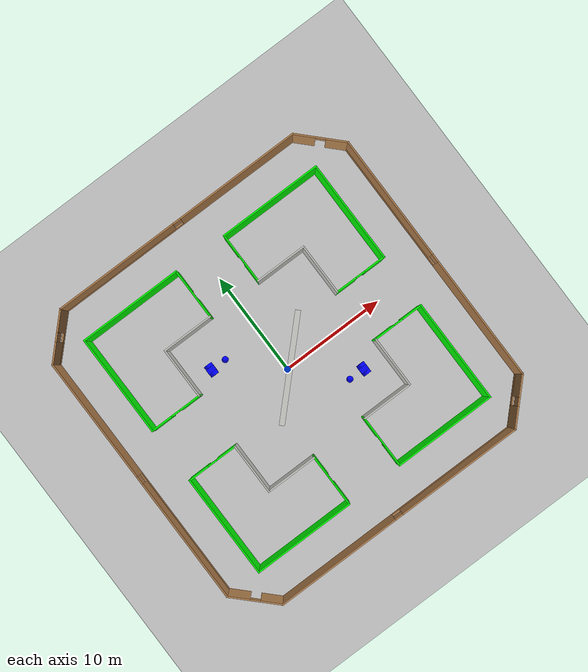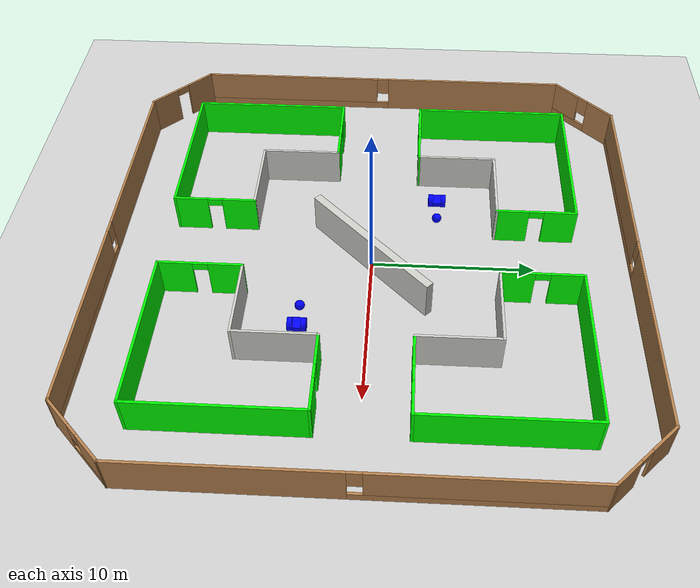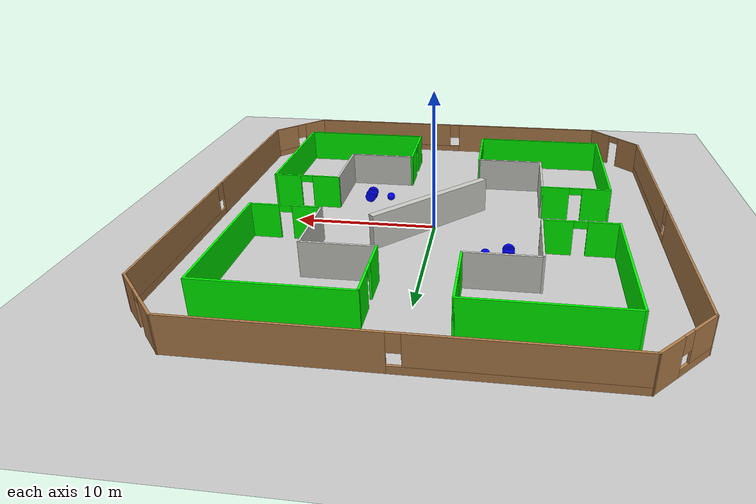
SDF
<sdf version="1.6">
 <world name="default">
  <include><uri>model://slash</uri><static>1</static></include>
  <include><uri>model://spheric_horse</uri><name>carriage1</name><pose>-5 4 0.5 0 0 0</pose></include>
  <include><uri>model://spheric_horse</uri><name>carriage2</name><pose>5 -4 0.5 0 0 3.1416</pose></include>
  <include><uri>model://my_ball</uri><name>white_ball</name><pose>0 3 0 0 0 0</pose></include>
  <light name="sun" type="directional">
   <pose>0 0 10 0 -0 0</pose>
   <diffuse>0.8 0.8 0.8 1</diffuse>
   <specular>0.2 0.2 0.2 1</specular>
   <attenuation>
    <range>1000</range>
    <constant>0.9</constant>
    <linear>0.01</linear>
    <quadratic>0.001</quadratic>
   </attenuation>
   <direction>-0.5 0.1 -0.9</direction>
  </light>
  <model name="ground_plane">
   <static>1</static>
   <link name="link">
    <collision name="collision">
     <geometry><plane><normal>0 0 1</normal><size>100 100</size></plane></geometry>
     <surface>
      <contact><collide_bitmask>65535</collide_bitmask></contact>
      <friction><ode><mu>100</mu><mu2>50</mu2></ode></friction>
     </surface>
    </collision>
    <visual name="visual">
     <cast_shadows>0</cast_shadows>
     <geometry><plane><normal>0 0 1</normal><size>100 100</size></plane></geometry>
     <material>
      <script><uri>file://media/materials/scripts/gazebo.material</uri><name>Gazebo/Grey</name></script>
     </material>
    </visual>
   </link>
  </model>
  <gravity>0 0 -9.8</gravity>
  <magnetic_field>6e-06 2.3e-05 -4.2e-05</magnetic_field>
  <atmosphere type="adiabatic"/>
  <physics name="default_physics" default="0" type="ode">
   <max_step_size>0.001</max_step_size>
   <real_time_factor>1</real_time_factor>
   <real_time_update_rate>1000</real_time_update_rate>
  </physics>
  <scene><ambient>0.4 0.4 0.4 1</ambient><background>0.7 0.7 0.7 1</background><shadows>1</shadows></scene>
  <audio><device>default</device></audio>
  <spherical_coordinates>
   <surface_model>EARTH_WGS84</surface_model>
   <latitude_deg>0</latitude_deg>
   <longitude_deg>0</longitude_deg>
   <elevation>0</elevation>
   <heading_deg>0</heading_deg>
  </spherical_coordinates>
 </world>
</sdf>

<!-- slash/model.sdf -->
<sdf version='1.6'>
  <model name='slash'>
    <pose frame=''>-8.48991 0.791123 0 0 -0 0</pose>
    <link name='Wall_12'>
      <pose frame=''>-14.1397 14.1397 0 0 -0 -2.35619</pose>
      <visual name='Wall_12_Visual_0'>
        <pose frame=''>-1.44919 0 1.25 0 -0 0</pose>
        <geometry>
          <box>
            <size>2.10162 0.15 2.5</size>
          </box>
        </geometry>
        <material>
          <script>
            <uri>file://media/materials/scripts/gazebo.material</uri>
            <name>Gazebo/Wood</name>
          </script>
          <ambient>1 1 1 1</ambient>
        </material>
        <meta>
          <layer>0</layer>
        </meta>
      </visual>
      <collision name='Wall_12_Collision_0'>
        <geometry>
          <box>
            <size>2.10162 0.15 2.5</size>
          </box>
        </geometry>
        <pose frame=''>-1.44919 0 1.25 0 -0 0</pose>
      </collision>
      <visual name='Wall_12_Visual_1'>
        <pose frame=''>1.05081 0 0.25 0 -0 0</pose>
        <geometry>
          <box>
            <size>2.89838 0.15 0.5</size>
          </box>
        </geometry>
        <material>
          <script>
            <uri>file://media/materials/scripts/gazebo.material</uri>
            <name>Gazebo/Wood</name>
          </script>
          <ambient>1 1 1 1</ambient>
        </material>
        <meta>
          <layer>0</layer>
        </meta>
      </visual>
      <collision name='Wall_12_Collision_1'>
        <geometry>
          <box>
            <size>2.89838 0.15 0.5</size>
          </box>
        </geometry>
        <pose frame=''>1.05081 0 0.25 0 -0 0</pose>
      </collision>
      <visual name='Wall_12_Visual_2'>
        <pose frame=''>1.45081 0 1.5 0 -0 0</pose>
        <geometry>
          <box>
            <size>2.09838 0.15 2</size>
          </box>
        </geometry>
        <material>
          <script>
            <uri>file://media/materials/scripts/gazebo.material</uri>
            <name>Gazebo/Wood</name>
          </script>
          <ambient>1 1 1 1</ambient>
        </material>
        <meta>
          <layer>0</layer>
        </meta>
      </visual>
      <collision name='Wall_12_Collision_2'>
        <geometry>
          <box>
            <size>2.09838 0.15 2</size>
          </box>
        </geometry>
        <pose frame=''>1.45081 0 1.5 0 -0 0</pose>
      </collision>
      <visual name='Wall_12_Visual_3'>
        <pose frame=''>0.00162 0 1.9 0 -0 0</pose>
        <geometry>
          <box>
            <size>0.8 0.15 1.2</size>
          </box>
        </geometry>
        <material>
          <script>
            <uri>file://media/materials/scripts/gazebo.material</uri>
            <name>Gazebo/Wood</name>
          </script>
          <ambient>1 1 1 1</ambient>
        </material>
        <meta>
          <layer>0</layer>
        </meta>
      </visual>
      <collision name='Wall_12_Collision_3'>
        <geometry>
          <box>
            <size>0.8 0.15 1.2</size>
          </box>
        </geometry>
        <pose frame=''>0.00162 0 1.9 0 -0 0</pose>
      </collision>
    </link>
    <link name='Wall_13'>
      <pose frame=''>-15.8545 1e-06 0 0 -0 -1.5708</pose>
      <visual name='Wall_13_Visual_0'>
        <pose frame=''>-6.46426 0 1.25 0 -0 0</pose>
        <geometry>
          <box>
            <size>12.0715 0.15 2.5</size>
          </box>
        </geometry>
        <material>
          <script>
            <uri>file://media/materials/scripts/gazebo.material</uri>
            <name>Gazebo/Wood</name>
          </script>
          <ambient>1 1 1 1</ambient>
        </material>
        <meta>
          <layer>0</layer>
        </meta>
      </visual>
      <collision name='Wall_13_Collision_0'>
        <geometry>
          <box>
            <size>12.0715 0.15 2.5</size>
          </box>
        </geometry>
        <pose frame=''>-6.46426 0 1.25 0 -0 0</pose>
      </collision>
      <visual name='Wall_13_Visual_1'>
        <pose frame=''>6.03574 0 0.25 0 -0 0</pose>
        <geometry>
          <box>
            <size>12.9285 0.15 0.5</size>
          </box>
        </geometry>
        <material>
          <script>
            <uri>file://media/materials/scripts/gazebo.material</uri>
            <name>Gazebo/Wood</name>
          </script>
          <ambient>1 1 1 1</ambient>
        </material>
        <meta>
          <layer>0</layer>
        </meta>
      </visual>
      <collision name='Wall_13_Collision_1'>
        <geometry>
          <box>
            <size>12.9285 0.15 0.5</size>
          </box>
        </geometry>
        <pose frame=''>6.03574 0 0.25 0 -0 0</pose>
      </collision>
      <visual name='Wall_13_Visual_2'>
        <pose frame=''>6.43574 0 1.5 0 -0 0</pose>
        <geometry>
          <box>
            <size>12.1285 0.15 2</size>
          </box>
        </geometry>
        <material>
          <script>
            <uri>file://media/materials/scripts/gazebo.material</uri>
            <name>Gazebo/Wood</name>
          </script>
          <ambient>1 1 1 1</ambient>
        </material>
        <meta>
          <layer>0</layer>
        </meta>
      </visual>
      <collision name='Wall_13_Collision_2'>
        <geometry>
          <box>
            <size>12.1285 0.15 2</size>
          </box>
        </geometry>
        <pose frame=''>6.43574 0 1.5 0 -0 0</pose>
      </collision>
      <visual name='Wall_13_Visual_3'>
        <pose frame=''>-0.02852 0 1.9 0 -0 0</pose>
        <geometry>
          <box>
            <size>0.8 0.15 1.2</size>
          </box>
        </geometry>
        <material>
          <script>
            <uri>file://media/materials/scripts/gazebo.material</uri>
            <name>Gazebo/Wood</name>
          </script>
          <ambient>1 1 1 1</ambient>
        </material>
        <meta>
          <layer>0</layer>
        </meta>
      </visual>
      <collision name='Wall_13_Collision_3'>
        <geometry>
          <box>
            <size>0.8 0.15 1.2</size>
          </box>
        </geometry>
        <pose frame=''>-0.02852 0 1.9 0 -0 0</pose>
      </collision>
    </link>
    <link name='Wall_14'>
      <pose frame=''>-14.1397 -14.1397 0 0 -0 -0.785398</pose>
      <visual name='Wall_14_Visual_0'>
        <pose frame=''>-1.4639 0 1.25 0 -0 0</pose>
        <geometry>
          <box>
            <size>2.07221 0.15 2.5</size>
          </box>
        </geometry>
        <material>
          <script>
            <uri>file://media/materials/scripts/gazebo.material</uri>
            <name>Gazebo/Wood</name>
          </script>
          <ambient>1 1 1 1</ambient>
        </material>
        <meta>
          <layer>0</layer>
        </meta>
      </visual>
      <collision name='Wall_14_Collision_0'>
        <geometry>
          <box>
            <size>2.07221 0.15 2.5</size>
          </box>
        </geometry>
        <pose frame=''>-1.4639 0 1.25 0 -0 0</pose>
      </collision>
      <visual name='Wall_14_Visual_1'>
        <pose frame=''>1.4861 0 1.25 0 -0 0</pose>
        <geometry>
          <box>
            <size>2.02779 0.15 2.5</size>
          </box>
        </geometry>
        <material>
          <script>
            <uri>file://media/materials/scripts/gazebo.material</uri>
            <name>Gazebo/Wood</name>
          </script>
          <ambient>1 1 1 1</ambient>
        </material>
        <meta>
          <layer>0</layer>
        </meta>
      </visual>
      <collision name='Wall_14_Collision_1'>
        <geometry>
          <box>
            <size>2.02779 0.15 2.5</size>
          </box>
        </geometry>
        <pose frame=''>1.4861 0 1.25 0 -0 0</pose>
      </collision>
      <visual name='Wall_14_Visual_2'>
        <pose frame=''>0.022208 0 2.25 0 -0 0</pose>
        <geometry>
          <box>
            <size>0.9 0.15 0.5</size>
          </box>
        </geometry>
        <material>
          <script>
            <uri>file://media/materials/scripts/gazebo.material</uri>
            <name>Gazebo/Wood</name>
          </script>
          <ambient>1 1 1 1</ambient>
        </material>
        <meta>
          <layer>0</layer>
        </meta>
      </visual>
      <collision name='Wall_14_Collision_2'>
        <geometry>
          <box>
            <size>0.9 0.15 0.5</size>
          </box>
        </geometry>
        <pose frame=''>0.022208 0 2.25 0 -0 0</pose>
      </collision>
    </link>
    <link name='Wall_24'>
      <collision name='Wall_24_Collision'>
        <geometry>
          <box>
            <size>10 0.15 2.5</size>
          </box>
        </geometry>
        <pose frame=''>0 0 1.25 0 -0 0</pose>
      </collision>
      <visual name='Wall_24_Visual'>
        <pose frame=''>0 0 1.25 0 -0 0</pose>
        <geometry>
          <box>
            <size>10 0.15 2.5</size>
          </box>
        </geometry>
        <material>
          <script>
            <uri>file://media/materials/scripts/gazebo.material</uri>
            <name>Gazebo/Grey</name>
          </script>
          <ambient>0 1 0 1</ambient>
        </material>
        <meta>
          <layer>0</layer>
        </meta>
      </visual>
      <pose frame=''>-7.50657 12.4595 0 0 -0 0</pose>
    </link>
    <link name='Wall_26'>
      <collision name='Wall_26_Collision'>
        <geometry>
          <box>
            <size>10 0.15 2.5</size>
          </box>
        </geometry>
        <pose frame=''>0 0 1.25 0 -0 0</pose>
      </collision>
      <visual name='Wall_26_Visual'>
        <pose frame=''>0 0 1.25 0 -0 0</pose>
        <geometry>
          <box>
            <size>10 0.15 2.5</size>
          </box>
        </geometry>
        <material>
          <script>
            <uri>file://media/materials/scripts/gazebo.material</uri>
            <name>Gazebo/Grey</name>
          </script>
          <ambient>0 1 0 1</ambient>
        </material>
        <meta>
          <layer>0</layer>
        </meta>
      </visual>
      <pose frame=''>7.47519 12.4293 0 0 -0 3.14159</pose>
    </link>
    <link name='Wall_27'>
      <pose frame=''>2.55019 10.0043 0 0 -0 -1.5708</pose>
      <visual name='Wall_27_Visual_0'>
        <pose frame=''>-1.49279 0 1.25 0 -0 0</pose>
        <geometry>
          <box>
            <size>2.01441 0.15 2.5</size>
          </box>
        </geometry>
        <material>
          <script>
            <uri>file://media/materials/scripts/gazebo.material</uri>
            <name>Gazebo/Grey</name>
          </script>
          <ambient>0 1 0 1</ambient>
        </material>
        <meta>
          <layer>0</layer>
        </meta>
      </visual>
      <collision name='Wall_27_Collision_0'>
        <geometry>
          <box>
            <size>2.01441 0.15 2.5</size>
          </box>
        </geometry>
        <pose frame=''>-1.49279 0 1.25 0 -0 0</pose>
      </collision>
      <visual name='Wall_27_Visual_1'>
        <pose frame=''>1.45721 0 1.25 0 -0 0</pose>
        <geometry>
          <box>
            <size>2.08559 0.15 2.5</size>
          </box>
        </geometry>
        <material>
          <script>
            <uri>file://media/materials/scripts/gazebo.material</uri>
            <name>Gazebo/Grey</name>
          </script>
          <ambient>0 1 0 1</ambient>
        </material>
        <meta>
          <layer>0</layer>
        </meta>
      </visual>
      <collision name='Wall_27_Collision_1'>
        <geometry>
          <box>
            <size>2.08559 0.15 2.5</size>
          </box>
        </geometry>
        <pose frame=''>1.45721 0 1.25 0 -0 0</pose>
      </collision>
      <visual name='Wall_27_Visual_2'>
        <pose frame=''>-0.035586 0 2.25 0 -0 0</pose>
        <geometry>
          <box>
            <size>0.9 0.15 0.5</size>
          </box>
        </geometry>
        <material>
          <script>
            <uri>file://media/materials/scripts/gazebo.material</uri>
            <name>Gazebo/Grey</name>
          </script>
          <ambient>0 1 0 1</ambient>
        </material>
        <meta>
          <layer>0</layer>
        </meta>
      </visual>
      <collision name='Wall_27_Collision_2'>
        <geometry>
          <box>
            <size>0.9 0.15 0.5</size>
          </box>
        </geometry>
        <pose frame=''>-0.035586 0 2.25 0 -0 0</pose>
      </collision>
    </link>
    <link name='Wall_28'>
      <collision name='Wall_28_Collision'>
        <geometry>
          <box>
            <size>5 0.15 2.5</size>
          </box>
        </geometry>
        <pose frame=''>0 0 1.25 0 -0 0</pose>
      </collision>
      <visual name='Wall_28_Visual'>
        <pose frame=''>0 0 1.25 0 -0 0</pose>
        <geometry>
          <box>
            <size>5 0.15 2.5</size>
          </box>
        </geometry>
        <material>
          <script>
            <uri>file://media/materials/scripts/gazebo.material</uri>
            <name>Gazebo/CeilingTiled</name>
          </script>
          <ambient>0.972549 0.458824 0.737255 1</ambient>
        </material>
        <meta>
          <layer>0</layer>
        </meta>
      </visual>
      <pose frame=''>4.97519 7.57928 0 0 -0 0</pose>
    </link>
    <link name='Wall_3'>
      <pose frame=''>0.030248 -15.8545 0 0 -0 0</pose>
      <visual name='Wall_3_Visual_0'>
        <pose frame=''>-6.46541 0 1.25 0 -0 0</pose>
        <geometry>
          <box>
            <size>12.1297 0.15 2.5</size>
          </box>
        </geometry>
        <material>
          <script>
            <uri>file://media/materials/scripts/gazebo.material</uri>
            <name>Gazebo/Wood</name>
          </script>
          <ambient>1 1 1 1</ambient>
        </material>
        <meta>
          <layer>0</layer>
        </meta>
      </visual>
      <collision name='Wall_3_Collision_0'>
        <geometry>
          <box>
            <size>12.1297 0.15 2.5</size>
          </box>
        </geometry>
        <pose frame=''>-6.46541 0 1.25 0 -0 0</pose>
      </collision>
      <visual name='Wall_3_Visual_1'>
        <pose frame=''>6.06484 0 0.25 0 -0 0</pose>
        <geometry>
          <box>
            <size>12.9308 0.15 0.5</size>
          </box>
        </geometry>
        <material>
          <script>
            <uri>file://media/materials/scripts/gazebo.material</uri>
            <name>Gazebo/Wood</name>
          </script>
          <ambient>1 1 1 1</ambient>
        </material>
        <meta>
          <layer>0</layer>
        </meta>
      </visual>
      <collision name='Wall_3_Collision_1'>
        <geometry>
          <box>
            <size>12.9308 0.15 0.5</size>
          </box>
        </geometry>
        <pose frame=''>6.06484 0 0.25 0 -0 0</pose>
      </collision>
      <visual name='Wall_3_Visual_2'>
        <pose frame=''>6.46484 0 1.5 0 -0 0</pose>
        <geometry>
          <box>
            <size>12.1308 0.15 2</size>
          </box>
        </geometry>
        <material>
          <script>
            <uri>file://media/materials/scripts/gazebo.material</uri>
            <name>Gazebo/Wood</name>
          </script>
          <ambient>1 1 1 1</ambient>
        </material>
        <meta>
          <layer>0</layer>
        </meta>
      </visual>
      <collision name='Wall_3_Collision_2'>
        <geometry>
          <box>
            <size>12.1308 0.15 2</size>
          </box>
        </geometry>
        <pose frame=''>6.46484 0 1.5 0 -0 0</pose>
      </collision>
      <visual name='Wall_3_Visual_3'>
        <pose frame=''>-0.000566 0 1.9 0 -0 0</pose>
        <geometry>
          <box>
            <size>0.8 0.15 1.2</size>
          </box>
        </geometry>
        <material>
          <script>
            <uri>file://media/materials/scripts/gazebo.material</uri>
            <name>Gazebo/Wood</name>
          </script>
          <ambient>1 1 1 1</ambient>
        </material>
        <meta>
          <layer>0</layer>
        </meta>
      </visual>
      <collision name='Wall_3_Collision_3'>
        <geometry>
          <box>
            <size>0.8 0.15 1.2</size>
          </box>
        </geometry>
        <pose frame=''>-0.000566 0 1.9 0 -0 0</pose>
      </collision>
    </link>
    <link name='Wall_32'>
      <collision name='Wall_32_Collision'>
        <geometry>
          <box>
            <size>5 0.15 2.5</size>
          </box>
        </geometry>
        <pose frame=''>0 0 1.25 0 -0 0</pose>
      </collision>
      <visual name='Wall_32_Visual'>
        <pose frame=''>0 0 1.25 0 -0 0</pose>
        <geometry>
          <box>
            <size>5 0.15 2.5</size>
          </box>
        </geometry>
        <material>
          <script>
            <uri>file://media/materials/scripts/gazebo.material</uri>
            <name>Gazebo/CeilingTiled</name>
          </script>
          <ambient>0.972549 0.458824 0.737255 1</ambient>
        </material>
        <meta>
          <layer>0</layer>
        </meta>
      </visual>
      <pose frame=''>7.40005 5.15408 0 0 -0 -1.57086</pose>
    </link>
    <link name='Wall_33'>
      <pose frame=''>9.89991 2.72888 0 0 -0 0</pose>
      <visual name='Wall_33_Visual_0'>
        <pose frame=''>-1.51755 0 1.25 0 -0 0</pose>
        <geometry>
          <box>
            <size>2.11489 0.15 2.5</size>
          </box>
        </geometry>
        <material>
          <script>
            <uri>file://media/materials/scripts/gazebo.material</uri>
            <name>Gazebo/Grey</name>
          </script>
          <ambient>0 1 0 1</ambient>
        </material>
        <meta>
          <layer>0</layer>
        </meta>
      </visual>
      <collision name='Wall_33_Collision_0'>
        <geometry>
          <box>
            <size>2.11489 0.15 2.5</size>
          </box>
        </geometry>
        <pose frame=''>-1.51755 0 1.25 0 -0 0</pose>
      </collision>
      <visual name='Wall_33_Visual_1'>
        <pose frame=''>1.50744 0 1.25 0 -0 0</pose>
        <geometry>
          <box>
            <size>2.13511 0.15 2.5</size>
          </box>
        </geometry>
        <material>
          <script>
            <uri>file://media/materials/scripts/gazebo.material</uri>
            <name>Gazebo/Grey</name>
          </script>
          <ambient>0 1 0 1</ambient>
        </material>
        <meta>
          <layer>0</layer>
        </meta>
      </visual>
      <collision name='Wall_33_Collision_1'>
        <geometry>
          <box>
            <size>2.13511 0.15 2.5</size>
          </box>
        </geometry>
        <pose frame=''>1.50744 0 1.25 0 -0 0</pose>
      </collision>
      <visual name='Wall_33_Visual_2'>
        <pose frame=''>-0.01011 0 2.25 0 -0 0</pose>
        <geometry>
          <box>
            <size>0.9 0.15 0.5</size>
          </box>
        </geometry>
        <material>
          <script>
            <uri>file://media/materials/scripts/gazebo.material</uri>
            <name>Gazebo/Grey</name>
          </script>
          <ambient>0 1 0 1</ambient>
        </material>
        <meta>
          <layer>0</layer>
        </meta>
      </visual>
      <collision name='Wall_33_Collision_2'>
        <geometry>
          <box>
            <size>0.9 0.15 0.5</size>
          </box>
        </geometry>
        <pose frame=''>-0.01011 0 2.25 0 -0 0</pose>
      </collision>
    </link>
    <link name='Wall_36'>
      <collision name='Wall_36_Collision'>
        <geometry>
          <box>
            <size>9.8504 0.15 2.5</size>
          </box>
        </geometry>
        <pose frame=''>0 0 1.25 0 -0 0</pose>
      </collision>
      <visual name='Wall_36_Visual'>
        <pose frame=''>0 0 1.25 0 -0 0</pose>
        <geometry>
          <box>
            <size>9.8504 0.15 2.5</size>
          </box>
        </geometry>
        <material>
          <script>
            <uri>file://media/materials/scripts/gazebo.material</uri>
            <name>Gazebo/Grey</name>
          </script>
          <ambient>0 1 0 1</ambient>
        </material>
        <meta>
          <layer>0</layer>
        </meta>
      </visual>
      <pose frame=''>12.4 7.57908 0 0 -0 1.57077</pose>
    </link>
    <link name='Wall_38'>
      <pose frame=''>-2.58157 10.0345 0 0 -0 -1.5708</pose>
      <visual name='Wall_38_Visual_0'>
        <pose frame=''>-1.47767 0 1.25 0 -0 0</pose>
        <geometry>
          <box>
            <size>2.04466 0.15 2.5</size>
          </box>
        </geometry>
        <material>
          <script>
            <uri>file://media/materials/scripts/gazebo.material</uri>
            <name>Gazebo/Grey</name>
          </script>
          <ambient>0 1 0 1</ambient>
        </material>
        <meta>
          <layer>0</layer>
        </meta>
      </visual>
      <collision name='Wall_38_Collision_0'>
        <geometry>
          <box>
            <size>2.04466 0.15 2.5</size>
          </box>
        </geometry>
        <pose frame=''>-1.47767 0 1.25 0 -0 0</pose>
      </collision>
      <visual name='Wall_38_Visual_1'>
        <pose frame=''>1.47233 0 1.25 0 -0 0</pose>
        <geometry>
          <box>
            <size>2.05534 0.15 2.5</size>
          </box>
        </geometry>
        <material>
          <script>
            <uri>file://media/materials/scripts/gazebo.material</uri>
            <name>Gazebo/Grey</name>
          </script>
          <ambient>0 1 0 1</ambient>
        </material>
        <meta>
          <layer>0</layer>
        </meta>
      </visual>
      <collision name='Wall_38_Collision_1'>
        <geometry>
          <box>
            <size>2.05534 0.15 2.5</size>
          </box>
        </geometry>
        <pose frame=''>1.47233 0 1.25 0 -0 0</pose>
      </collision>
      <visual name='Wall_38_Visual_2'>
        <pose frame=''>-0.005341 0 2.25 0 -0 0</pose>
        <geometry>
          <box>
            <size>0.9 0.15 0.5</size>
          </box>
        </geometry>
        <material>
          <script>
            <uri>file://media/materials/scripts/gazebo.material</uri>
            <name>Gazebo/Grey</name>
          </script>
          <ambient>0 1 0 1</ambient>
        </material>
        <meta>
          <layer>0</layer>
        </meta>
      </visual>
      <collision name='Wall_38_Collision_2'>
        <geometry>
          <box>
            <size>0.9 0.15 0.5</size>
          </box>
        </geometry>
        <pose frame=''>-0.005341 0 2.25 0 -0 0</pose>
      </collision>
    </link>
    <link name='Wall_39'>
      <collision name='Wall_39_Collision'>
        <geometry>
          <box>
            <size>5 0.15 2.5</size>
          </box>
        </geometry>
        <pose frame=''>0 0 1.25 0 -0 0</pose>
      </collision>
      <visual name='Wall_39_Visual'>
        <pose frame=''>0 0 1.25 0 -0 0</pose>
        <geometry>
          <box>
            <size>5 0.15 2.5</size>
          </box>
        </geometry>
        <material>
          <script>
            <uri>file://media/materials/scripts/gazebo.material</uri>
            <name>Gazebo/CeilingTiled</name>
          </script>
          <ambient>0.972549 0.458824 0.737255 1</ambient>
        </material>
        <meta>
          <layer>0</layer>
        </meta>
      </visual>
      <pose frame=''>-5.00657 7.60952 0 0 -0 3.14159</pose>
    </link>
    <link name='Wall_4'>
      <pose frame=''>14.17 -14.1397 0 0 -0 0.794296</pose>
      <visual name='Wall_4_Visual_0'>
        <pose frame=''>-1.44007 0 1.25 0 -0 0</pose>
        <geometry>
          <box>
            <size>2.07727 0.15 2.5</size>
          </box>
        </geometry>
        <material>
          <script>
            <uri>file://media/materials/scripts/gazebo.material</uri>
            <name>Gazebo/Wood</name>
          </script>
          <ambient>1 1 1 1</ambient>
        </material>
        <meta>
          <layer>0</layer>
        </meta>
      </visual>
      <collision name='Wall_4_Collision_0'>
        <geometry>
          <box>
            <size>2.07727 0.15 2.5</size>
          </box>
        </geometry>
        <pose frame=''>-1.44007 0 1.25 0 -0 0</pose>
      </collision>
      <visual name='Wall_4_Visual_1'>
        <pose frame=''>1.03863 0 0.25 0 -0 0</pose>
        <geometry>
          <box>
            <size>2.88015 0.15 0.5</size>
          </box>
        </geometry>
        <material>
          <script>
            <uri>file://media/materials/scripts/gazebo.material</uri>
            <name>Gazebo/Wood</name>
          </script>
          <ambient>1 1 1 1</ambient>
        </material>
        <meta>
          <layer>0</layer>
        </meta>
      </visual>
      <collision name='Wall_4_Collision_1'>
        <geometry>
          <box>
            <size>2.88015 0.15 0.5</size>
          </box>
        </geometry>
        <pose frame=''>1.03863 0 0.25 0 -0 0</pose>
      </collision>
      <visual name='Wall_4_Visual_2'>
        <pose frame=''>1.43863 0 1.5 0 -0 0</pose>
        <geometry>
          <box>
            <size>2.08015 0.15 2</size>
          </box>
        </geometry>
        <material>
          <script>
            <uri>file://media/materials/scripts/gazebo.material</uri>
            <name>Gazebo/Wood</name>
          </script>
          <ambient>1 1 1 1</ambient>
        </material>
        <meta>
          <layer>0</layer>
        </meta>
      </visual>
      <collision name='Wall_4_Collision_2'>
        <geometry>
          <box>
            <size>2.08015 0.15 2</size>
          </box>
        </geometry>
        <pose frame=''>1.43863 0 1.5 0 -0 0</pose>
      </collision>
      <visual name='Wall_4_Visual_3'>
        <pose frame=''>-0.00144 0 1.9 0 -0 0</pose>
        <geometry>
          <box>
            <size>0.8 0.15 1.2</size>
          </box>
        </geometry>
        <material>
          <script>
            <uri>file://media/materials/scripts/gazebo.material</uri>
            <name>Gazebo/Wood</name>
          </script>
          <ambient>1 1 1 1</ambient>
        </material>
        <meta>
          <layer>0</layer>
        </meta>
      </visual>
      <collision name='Wall_4_Collision_3'>
        <geometry>
          <box>
            <size>0.8 0.15 1.2</size>
          </box>
        </geometry>
        <pose frame=''>-0.00144 0 1.9 0 -0 0</pose>
      </collision>
    </link>
    <link name='Wall_40'>
      <collision name='Wall_40_Collision'>
        <geometry>
          <box>
            <size>5 0.15 2.5</size>
          </box>
        </geometry>
        <pose frame=''>0 0 1.25 0 -0 0</pose>
      </collision>
      <visual name='Wall_40_Visual'>
        <pose frame=''>0 0 1.25 0 -0 0</pose>
        <geometry>
          <box>
            <size>5 0.15 2.5</size>
          </box>
        </geometry>
        <material>
          <script>
            <uri>file://media/materials/scripts/gazebo.material</uri>
            <name>Gazebo/CeilingTiled</name>
          </script>
          <ambient>0.972549 0.458824 0.737255 1</ambient>
        </material>
        <meta>
          <layer>0</layer>
        </meta>
      </visual>
      <pose frame=''>-7.43133 5.1847 0 0 -0 -1.5707</pose>
    </link>
    <link name='Wall_41'>
      <pose frame=''>-9.93109 2.75988 0 0 -0 3.14159</pose>
      <visual name='Wall_41_Visual_0'>
        <pose frame=''>-1.51746 0 1.25 0 -0 0</pose>
        <geometry>
          <box>
            <size>2.11507 0.15 2.5</size>
          </box>
        </geometry>
        <material>
          <script>
            <uri>file://media/materials/scripts/gazebo.material</uri>
            <name>Gazebo/Grey</name>
          </script>
          <ambient>0 1 0 1</ambient>
        </material>
        <meta>
          <layer>0</layer>
        </meta>
      </visual>
      <collision name='Wall_41_Collision_0'>
        <geometry>
          <box>
            <size>2.11507 0.15 2.5</size>
          </box>
        </geometry>
        <pose frame=''>-1.51746 0 1.25 0 -0 0</pose>
      </collision>
      <visual name='Wall_41_Visual_1'>
        <pose frame=''>1.50754 0 1.25 0 -0 0</pose>
        <geometry>
          <box>
            <size>2.13493 0.15 2.5</size>
          </box>
        </geometry>
        <material>
          <script>
            <uri>file://media/materials/scripts/gazebo.material</uri>
            <name>Gazebo/Grey</name>
          </script>
          <ambient>0 1 0 1</ambient>
        </material>
        <meta>
          <layer>0</layer>
        </meta>
      </visual>
      <collision name='Wall_41_Collision_1'>
        <geometry>
          <box>
            <size>2.13493 0.15 2.5</size>
          </box>
        </geometry>
        <pose frame=''>1.50754 0 1.25 0 -0 0</pose>
      </collision>
      <visual name='Wall_41_Visual_2'>
        <pose frame=''>-0.009926 0 2.25 0 -0 0</pose>
        <geometry>
          <box>
            <size>0.9 0.15 0.5</size>
          </box>
        </geometry>
        <material>
          <script>
            <uri>file://media/materials/scripts/gazebo.material</uri>
            <name>Gazebo/Grey</name>
          </script>
          <ambient>0 1 0 1</ambient>
        </material>
        <meta>
          <layer>0</layer>
        </meta>
      </visual>
      <collision name='Wall_41_Collision_2'>
        <geometry>
          <box>
            <size>0.9 0.15 0.5</size>
          </box>
        </geometry>
        <pose frame=''>-0.009926 0 2.25 0 -0 0</pose>
      </collision>
    </link>
    <link name='Wall_43'>
      <collision name='Wall_43_Collision'>
        <geometry>
          <box>
            <size>9.84965 0.15 2.5</size>
          </box>
        </geometry>
        <pose frame=''>0 0 1.25 0 -0 0</pose>
      </collision>
      <visual name='Wall_43_Visual'>
        <pose frame=''>0 0 1.25 0 -0 0</pose>
        <geometry>
          <box>
            <size>9.84965 0.15 2.5</size>
          </box>
        </geometry>
        <material>
          <script>
            <uri>file://media/materials/scripts/gazebo.material</uri>
            <name>Gazebo/Grey</name>
          </script>
          <ambient>0 1 0 1</ambient>
        </material>
        <meta>
          <layer>0</layer>
        </meta>
      </visual>
      <pose frame=''>-12.4313 7.6097 0 0 -0 1.57085</pose>
    </link>
    <link name='Wall_45'>
      <collision name='Wall_45_Collision'>
        <geometry>
          <box>
            <size>10 0.15 2.5</size>
          </box>
        </geometry>
        <pose frame=''>0 0 1.25 0 -0 0</pose>
      </collision>
      <visual name='Wall_45_Visual'>
        <pose frame=''>0 0 1.25 0 -0 0</pose>
        <geometry>
          <box>
            <size>10 0.15 2.5</size>
          </box>
        </geometry>
        <material>
          <script>
            <uri>file://media/materials/scripts/gazebo.material</uri>
            <name>Gazebo/Grey</name>
          </script>
          <ambient>0 1 0 1</ambient>
        </material>
        <meta>
          <layer>0</layer>
        </meta>
      </visual>
      <pose frame=''>-12.4316 -7.47748 0 0 -0 1.5708</pose>
    </link>
    <link name='Wall_46'>
      <pose frame=''>-10.0066 -2.55248 0 0 -0 0</pose>
      <visual name='Wall_46_Visual_0'>
        <pose frame=''>-1.46255 0 1.25 0 -0 0</pose>
        <geometry>
          <box>
            <size>2.07491 0.15 2.5</size>
          </box>
        </geometry>
        <material>
          <script>
            <uri>file://media/materials/scripts/gazebo.material</uri>
            <name>Gazebo/Grey</name>
          </script>
          <ambient>0 1 0 1</ambient>
        </material>
        <meta>
          <layer>0</layer>
        </meta>
      </visual>
      <collision name='Wall_46_Collision_0'>
        <geometry>
          <box>
            <size>2.07491 0.15 2.5</size>
          </box>
        </geometry>
        <pose frame=''>-1.46255 0 1.25 0 -0 0</pose>
      </collision>
      <visual name='Wall_46_Visual_1'>
        <pose frame=''>1.48745 0 1.25 0 -0 0</pose>
        <geometry>
          <box>
            <size>2.02509 0.15 2.5</size>
          </box>
        </geometry>
        <material>
          <script>
            <uri>file://media/materials/scripts/gazebo.material</uri>
            <name>Gazebo/Grey</name>
          </script>
          <ambient>0 1 0 1</ambient>
        </material>
        <meta>
          <layer>0</layer>
        </meta>
      </visual>
      <collision name='Wall_46_Collision_1'>
        <geometry>
          <box>
            <size>2.02509 0.15 2.5</size>
          </box>
        </geometry>
        <pose frame=''>1.48745 0 1.25 0 -0 0</pose>
      </collision>
      <visual name='Wall_46_Visual_2'>
        <pose frame=''>0.024906 0 2.25 0 -0 0</pose>
        <geometry>
          <box>
            <size>0.9 0.15 0.5</size>
          </box>
        </geometry>
        <material>
          <script>
            <uri>file://media/materials/scripts/gazebo.material</uri>
            <name>Gazebo/Grey</name>
          </script>
          <ambient>0 1 0 1</ambient>
        </material>
        <meta>
          <layer>0</layer>
        </meta>
      </visual>
      <collision name='Wall_46_Collision_2'>
        <geometry>
          <box>
            <size>0.9 0.15 0.5</size>
          </box>
        </geometry>
        <pose frame=''>0.024906 0 2.25 0 -0 0</pose>
      </collision>
    </link>
    <link name='Wall_47'>
      <collision name='Wall_47_Collision'>
        <geometry>
          <box>
            <size>5 0.15 2.5</size>
          </box>
        </geometry>
        <pose frame=''>0 0 1.25 0 -0 0</pose>
      </collision>
      <visual name='Wall_47_Visual'>
        <pose frame=''>0 0 1.25 0 -0 0</pose>
        <geometry>
          <box>
            <size>5 0.15 2.5</size>
          </box>
        </geometry>
        <material>
          <script>
            <uri>file://media/materials/scripts/gazebo.material</uri>
            <name>Gazebo/CeilingTiled</name>
          </script>
          <ambient>1 0.580392 0.909804 1</ambient>
        </material>
        <meta>
          <layer>0</layer>
        </meta>
      </visual>
      <pose frame=''>-7.58157 -4.97748 0 0 -0 -1.5708</pose>
    </link>
    <link name='Wall_48'>
      <collision name='Wall_48_Collision'>
        <geometry>
          <box>
            <size>5 0.15 2.5</size>
          </box>
        </geometry>
        <pose frame=''>0 0 1.25 0 -0 0</pose>
      </collision>
      <visual name='Wall_48_Visual'>
        <pose frame=''>0 0 1.25 0 -0 0</pose>
        <geometry>
          <box>
            <size>5 0.15 2.5</size>
          </box>
        </geometry>
        <material>
          <script>
            <uri>file://media/materials/scripts/gazebo.material</uri>
            <name>Gazebo/CeilingTiled</name>
          </script>
          <ambient>0.972549 0.458824 0.737255 1</ambient>
        </material>
        <meta>
          <layer>0</layer>
        </meta>
      </visual>
      <pose frame=''>-5.15633 -7.4023 0 0 -0 7.4e-05</pose>
    </link>
    <link name='Wall_49'>
      <pose frame=''>-2.73109 -9.90212 0 0 -0 -1.5708</pose>
      <visual name='Wall_49_Visual_0'>
        <pose frame=''>-1.51752 0 1.25 0 -0 0</pose>
        <geometry>
          <box>
            <size>2.11496 0.15 2.5</size>
          </box>
        </geometry>
        <material>
          <script>
            <uri>file://media/materials/scripts/gazebo.material</uri>
            <name>Gazebo/Grey</name>
          </script>
          <ambient>0 1 0 1</ambient>
        </material>
        <meta>
          <layer>0</layer>
        </meta>
      </visual>
      <collision name='Wall_49_Collision_0'>
        <geometry>
          <box>
            <size>2.11496 0.15 2.5</size>
          </box>
        </geometry>
        <pose frame=''>-1.51752 0 1.25 0 -0 0</pose>
      </collision>
      <visual name='Wall_49_Visual_1'>
        <pose frame=''>1.50748 0 1.25 0 -0 0</pose>
        <geometry>
          <box>
            <size>2.13504 0.15 2.5</size>
          </box>
        </geometry>
        <material>
          <script>
            <uri>file://media/materials/scripts/gazebo.material</uri>
            <name>Gazebo/Grey</name>
          </script>
          <ambient>0 1 0 1</ambient>
        </material>
        <meta>
          <layer>0</layer>
        </meta>
      </visual>
      <collision name='Wall_49_Collision_1'>
        <geometry>
          <box>
            <size>2.13504 0.15 2.5</size>
          </box>
        </geometry>
        <pose frame=''>1.50748 0 1.25 0 -0 0</pose>
      </collision>
      <visual name='Wall_49_Visual_2'>
        <pose frame=''>-0.010039 0 2.25 0 -0 0</pose>
        <geometry>
          <box>
            <size>0.9 0.15 0.5</size>
          </box>
        </geometry>
        <material>
          <script>
            <uri>file://media/materials/scripts/gazebo.material</uri>
            <name>Gazebo/Grey</name>
          </script>
          <ambient>0 1 0 1</ambient>
        </material>
        <meta>
          <layer>0</layer>
        </meta>
      </visual>
      <collision name='Wall_49_Collision_2'>
        <geometry>
          <box>
            <size>0.9 0.15 0.5</size>
          </box>
        </geometry>
        <pose frame=''>-0.010039 0 2.25 0 -0 0</pose>
      </collision>
    </link>
    <link name='Wall_5'>
      <pose frame=''>15.8545 1e-06 0 0 -0 1.5708</pose>
      <visual name='Wall_5_Visual_0'>
        <pose frame=''>-6.45086 0 1.25 0 -0 0</pose>
        <geometry>
          <box>
            <size>12.0983 0.15 2.5</size>
          </box>
        </geometry>
        <material>
          <script>
            <uri>file://media/materials/scripts/gazebo.material</uri>
            <name>Gazebo/Wood</name>
          </script>
          <ambient>1 1 1 1</ambient>
        </material>
        <meta>
          <layer>0</layer>
        </meta>
      </visual>
      <collision name='Wall_5_Collision_0'>
        <geometry>
          <box>
            <size>12.0983 0.15 2.5</size>
          </box>
        </geometry>
        <pose frame=''>-6.45086 0 1.25 0 -0 0</pose>
      </collision>
      <visual name='Wall_5_Visual_1'>
        <pose frame=''>6.04914 0 0.25 0 -0 0</pose>
        <geometry>
          <box>
            <size>12.9017 0.15 0.5</size>
          </box>
        </geometry>
        <material>
          <script>
            <uri>file://media/materials/scripts/gazebo.material</uri>
            <name>Gazebo/Wood</name>
          </script>
          <ambient>1 1 1 1</ambient>
        </material>
        <meta>
          <layer>0</layer>
        </meta>
      </visual>
      <collision name='Wall_5_Collision_1'>
        <geometry>
          <box>
            <size>12.9017 0.15 0.5</size>
          </box>
        </geometry>
        <pose frame=''>6.04914 0 0.25 0 -0 0</pose>
      </collision>
      <visual name='Wall_5_Visual_2'>
        <pose frame=''>6.44914 0 1.5 0 -0 0</pose>
        <geometry>
          <box>
            <size>12.1017 0.15 2</size>
          </box>
        </geometry>
        <material>
          <script>
            <uri>file://media/materials/scripts/gazebo.material</uri>
            <name>Gazebo/Wood</name>
          </script>
          <ambient>1 1 1 1</ambient>
        </material>
        <meta>
          <layer>0</layer>
        </meta>
      </visual>
      <collision name='Wall_5_Collision_2'>
        <geometry>
          <box>
            <size>12.1017 0.15 2</size>
          </box>
        </geometry>
        <pose frame=''>6.44914 0 1.5 0 -0 0</pose>
      </collision>
      <visual name='Wall_5_Visual_3'>
        <pose frame=''>-0.001726 0 1.9 0 -0 0</pose>
        <geometry>
          <box>
            <size>0.8 0.15 1.2</size>
          </box>
        </geometry>
        <material>
          <script>
            <uri>file://media/materials/scripts/gazebo.material</uri>
            <name>Gazebo/Wood</name>
          </script>
          <ambient>1 1 1 1</ambient>
        </material>
        <meta>
          <layer>0</layer>
        </meta>
      </visual>
      <collision name='Wall_5_Collision_3'>
        <geometry>
          <box>
            <size>0.8 0.15 1.2</size>
          </box>
        </geometry>
        <pose frame=''>-0.001726 0 1.9 0 -0 0</pose>
      </collision>
    </link>
    <link name='Wall_51'>
      <collision name='Wall_51_Collision'>
        <geometry>
          <box>
            <size>9.85047 0.15 2.5</size>
          </box>
        </geometry>
        <pose frame=''>0 0 1.25 0 -0 0</pose>
      </collision>
      <visual name='Wall_51_Visual'>
        <pose frame=''>0 0 1.25 0 -0 0</pose>
        <geometry>
          <box>
            <size>9.85047 0.15 2.5</size>
          </box>
        </geometry>
        <material>
          <script>
            <uri>file://media/materials/scripts/gazebo.material</uri>
            <name>Gazebo/Grey</name>
          </script>
          <ambient>0 1 0 1</ambient>
        </material>
        <meta>
          <layer>0</layer>
        </meta>
      </visual>
      <pose frame=''>-7.58133 -12.4023 0 0 -0 -3.14156</pose>
    </link>
    <link name='Wall_54'>
      <collision name='Wall_54_Collision'>
        <geometry>
          <box>
            <size>10 0.15 2.5</size>
          </box>
        </geometry>
        <pose frame=''>0 0 1.25 0 -0 0</pose>
      </collision>
      <visual name='Wall_54_Visual'>
        <pose frame=''>0 0 1.25 0 -0 0</pose>
        <geometry>
          <box>
            <size>10 0.15 2.5</size>
          </box>
        </geometry>
        <material>
          <script>
            <uri>file://media/materials/scripts/gazebo.material</uri>
            <name>Gazebo/Grey</name>
          </script>
          <ambient>0 1 0 1</ambient>
        </material>
        <meta>
          <layer>0</layer>
        </meta>
      </visual>
      <pose frame=''>12.4304 -7.41699 0 0 -0 1.5708</pose>
    </link>
    <link name='Wall_55'>
      <pose frame=''>10.0054 -2.49199 0 0 -0 3.14159</pose>
      <visual name='Wall_55_Visual_0'>
        <pose frame=''>-1.47767 0 1.25 0 -0 0</pose>
        <geometry>
          <box>
            <size>2.04466 0.15 2.5</size>
          </box>
        </geometry>
        <material>
          <script>
            <uri>file://media/materials/scripts/gazebo.material</uri>
            <name>Gazebo/Grey</name>
          </script>
          <ambient>0 1 0 1</ambient>
        </material>
        <meta>
          <layer>0</layer>
        </meta>
      </visual>
      <collision name='Wall_55_Collision_0'>
        <geometry>
          <box>
            <size>2.04466 0.15 2.5</size>
          </box>
        </geometry>
        <pose frame=''>-1.47767 0 1.25 0 -0 0</pose>
      </collision>
      <visual name='Wall_55_Visual_1'>
        <pose frame=''>1.47233 0 1.25 0 -0 0</pose>
        <geometry>
          <box>
            <size>2.05534 0.15 2.5</size>
          </box>
        </geometry>
        <material>
          <script>
            <uri>file://media/materials/scripts/gazebo.material</uri>
            <name>Gazebo/Grey</name>
          </script>
          <ambient>0 1 0 1</ambient>
        </material>
        <meta>
          <layer>0</layer>
        </meta>
      </visual>
      <collision name='Wall_55_Collision_1'>
        <geometry>
          <box>
            <size>2.05534 0.15 2.5</size>
          </box>
        </geometry>
        <pose frame=''>1.47233 0 1.25 0 -0 0</pose>
      </collision>
      <visual name='Wall_55_Visual_2'>
        <pose frame=''>-0.00534 0 2.25 0 -0 0</pose>
        <geometry>
          <box>
            <size>0.9 0.15 0.5</size>
          </box>
        </geometry>
        <material>
          <script>
            <uri>file://media/materials/scripts/gazebo.material</uri>
            <name>Gazebo/Grey</name>
          </script>
          <ambient>0 1 0 1</ambient>
        </material>
        <meta>
          <layer>0</layer>
        </meta>
      </visual>
      <collision name='Wall_55_Collision_2'>
        <geometry>
          <box>
            <size>0.9 0.15 0.5</size>
          </box>
        </geometry>
        <pose frame=''>-0.00534 0 2.25 0 -0 0</pose>
      </collision>
    </link>
    <link name='Wall_56'>
      <collision name='Wall_56_Collision'>
        <geometry>
          <box>
            <size>5 0.15 2.5</size>
          </box>
        </geometry>
        <pose frame=''>0 0 1.25 0 -0 0</pose>
      </collision>
      <visual name='Wall_56_Visual'>
        <pose frame=''>0 0 1.25 0 -0 0</pose>
        <geometry>
          <box>
            <size>5 0.15 2.5</size>
          </box>
        </geometry>
        <material>
          <script>
            <uri>file://media/materials/scripts/gazebo.material</uri>
            <name>Gazebo/CeilingTiled</name>
          </script>
          <ambient>0.972549 0.458824 0.737255 1</ambient>
        </material>
        <meta>
          <layer>0</layer>
        </meta>
      </visual>
      <pose frame=''>7.58044 -4.91699 0 0 -0 -1.5708</pose>
    </link>
    <link name='Wall_57'>
      <collision name='Wall_57_Collision'>
        <geometry>
          <box>
            <size>5 0.15 2.5</size>
          </box>
        </geometry>
        <pose frame=''>0 0 1.25 0 -0 0</pose>
      </collision>
      <visual name='Wall_57_Visual'>
        <pose frame=''>0 0 1.25 0 -0 0</pose>
        <geometry>
          <box>
            <size>5 0.15 2.5</size>
          </box>
        </geometry>
        <material>
          <script>
            <uri>file://media/materials/scripts/gazebo.material</uri>
            <name>Gazebo/CeilingTiled</name>
          </script>
          <ambient>0.972549 0.458824 0.737255 1</ambient>
        </material>
        <meta>
          <layer>0</layer>
        </meta>
      </visual>
      <pose frame=''>5.15567 -7.34206 0 0 -0 -3.14156</pose>
    </link>
    <link name='Wall_58'>
      <pose frame=''>2.73091 -9.84212 0 0 -0 -1.5708</pose>
      <visual name='Wall_58_Visual_0'>
        <pose frame=''>-1.51777 0 1.25 0 -0 0</pose>
        <geometry>
          <box>
            <size>2.11447 0.15 2.5</size>
          </box>
        </geometry>
        <material>
          <script>
            <uri>file://media/materials/scripts/gazebo.material</uri>
            <name>Gazebo/Grey</name>
          </script>
          <ambient>0 1 0 1</ambient>
        </material>
        <meta>
          <layer>0</layer>
        </meta>
      </visual>
      <collision name='Wall_58_Collision_0'>
        <geometry>
          <box>
            <size>2.11447 0.15 2.5</size>
          </box>
        </geometry>
        <pose frame=''>-1.51777 0 1.25 0 -0 0</pose>
      </collision>
      <visual name='Wall_58_Visual_1'>
        <pose frame=''>1.50724 0 1.25 0 -0 0</pose>
        <geometry>
          <box>
            <size>2.13553 0.15 2.5</size>
          </box>
        </geometry>
        <material>
          <script>
            <uri>file://media/materials/scripts/gazebo.material</uri>
            <name>Gazebo/Grey</name>
          </script>
          <ambient>0 1 0 1</ambient>
        </material>
        <meta>
          <layer>0</layer>
        </meta>
      </visual>
      <collision name='Wall_58_Collision_1'>
        <geometry>
          <box>
            <size>2.13553 0.15 2.5</size>
          </box>
        </geometry>
        <pose frame=''>1.50724 0 1.25 0 -0 0</pose>
      </collision>
      <visual name='Wall_58_Visual_2'>
        <pose frame=''>-0.01053 0 2.25 0 -0 0</pose>
        <geometry>
          <box>
            <size>0.9 0.15 0.5</size>
          </box>
        </geometry>
        <material>
          <script>
            <uri>file://media/materials/scripts/gazebo.material</uri>
            <name>Gazebo/Grey</name>
          </script>
          <ambient>0 1 0 1</ambient>
        </material>
        <meta>
          <layer>0</layer>
        </meta>
      </visual>
      <collision name='Wall_58_Collision_2'>
        <geometry>
          <box>
            <size>0.9 0.15 0.5</size>
          </box>
        </geometry>
        <pose frame=''>-0.01053 0 2.25 0 -0 0</pose>
      </collision>
    </link>
    <link name='Wall_6'>
      <pose frame=''>14.17 14.1397 0 0 -0 2.3473</pose>
      <visual name='Wall_6_Visual_0'>
        <pose frame=''>-1.47584 0 1.25 0 -0 0</pose>
        <geometry>
          <box>
            <size>2.00573 0.15 2.5</size>
          </box>
        </geometry>
        <material>
          <script>
            <uri>file://media/materials/scripts/gazebo.material</uri>
            <name>Gazebo/Wood</name>
          </script>
          <ambient>1 1 1 1</ambient>
        </material>
        <meta>
          <layer>0</layer>
        </meta>
      </visual>
      <collision name='Wall_6_Collision_0'>
        <geometry>
          <box>
            <size>2.00573 0.15 2.5</size>
          </box>
        </geometry>
        <pose frame=''>-1.47584 0 1.25 0 -0 0</pose>
      </collision>
      <visual name='Wall_6_Visual_1'>
        <pose frame=''>1.45286 0 1.25 0 -0 0</pose>
        <geometry>
          <box>
            <size>2.05169 0.15 2.5</size>
          </box>
        </geometry>
        <material>
          <script>
            <uri>file://media/materials/scripts/gazebo.material</uri>
            <name>Gazebo/Wood</name>
          </script>
          <ambient>1 1 1 1</ambient>
        </material>
        <meta>
          <layer>0</layer>
        </meta>
      </visual>
      <collision name='Wall_6_Collision_1'>
        <geometry>
          <box>
            <size>2.05169 0.15 2.5</size>
          </box>
        </geometry>
        <pose frame=''>1.45286 0 1.25 0 -0 0</pose>
      </collision>
      <visual name='Wall_6_Visual_2'>
        <pose frame=''>-0.02298 0 2.25 0 -0 0</pose>
        <geometry>
          <box>
            <size>0.9 0.15 0.5</size>
          </box>
        </geometry>
        <material>
          <script>
            <uri>file://media/materials/scripts/gazebo.material</uri>
            <name>Gazebo/Wood</name>
          </script>
          <ambient>1 1 1 1</ambient>
        </material>
        <meta>
          <layer>0</layer>
        </meta>
      </visual>
      <collision name='Wall_6_Collision_2'>
        <geometry>
          <box>
            <size>0.9 0.15 0.5</size>
          </box>
        </geometry>
        <pose frame=''>-0.02298 0 2.25 0 -0 0</pose>
      </collision>
    </link>
    <link name='Wall_60'>
      <collision name='Wall_60_Collision'>
        <geometry>
          <box>
            <size>9.85 0.15 2.5</size>
          </box>
        </geometry>
        <pose frame=''>0 0 1.25 0 -0 0</pose>
      </collision>
      <visual name='Wall_60_Visual'>
        <pose frame=''>0 0 1.25 0 -0 0</pose>
        <geometry>
          <box>
            <size>9.85 0.15 2.5</size>
          </box>
        </geometry>
        <material>
          <script>
            <uri>file://media/materials/scripts/gazebo.material</uri>
            <name>Gazebo/Grey</name>
          </script>
          <ambient>0 1 0 1</ambient>
        </material>
        <meta>
          <layer>0</layer>
        </meta>
      </visual>
      <pose frame=''>7.5809 -12.3421 0 0 -0 0</pose>
    </link>
    <link name='Wall_7'>
      <pose frame=''>0.030248 15.8545 0 0 -0 3.14159</pose>
      <visual name='Wall_7_Visual_0'>
        <pose frame=''>-6.46484 0 1.25 0 -0 0</pose>
        <geometry>
          <box>
            <size>12.1308 0.15 2.5</size>
          </box>
        </geometry>
        <material>
          <script>
            <uri>file://media/materials/scripts/gazebo.material</uri>
            <name>Gazebo/Wood</name>
          </script>
          <ambient>1 1 1 1</ambient>
        </material>
        <meta>
          <layer>0</layer>
        </meta>
      </visual>
      <collision name='Wall_7_Collision_0'>
        <geometry>
          <box>
            <size>12.1308 0.15 2.5</size>
          </box>
        </geometry>
        <pose frame=''>-6.46484 0 1.25 0 -0 0</pose>
      </collision>
      <visual name='Wall_7_Visual_1'>
        <pose frame=''>6.06541 0 0.25 0 -0 0</pose>
        <geometry>
          <box>
            <size>12.9297 0.15 0.5</size>
          </box>
        </geometry>
        <material>
          <script>
            <uri>file://media/materials/scripts/gazebo.material</uri>
            <name>Gazebo/Wood</name>
          </script>
          <ambient>1 1 1 1</ambient>
        </material>
        <meta>
          <layer>0</layer>
        </meta>
      </visual>
      <collision name='Wall_7_Collision_1'>
        <geometry>
          <box>
            <size>12.9297 0.15 0.5</size>
          </box>
        </geometry>
        <pose frame=''>6.06541 0 0.25 0 -0 0</pose>
      </collision>
      <visual name='Wall_7_Visual_2'>
        <pose frame=''>6.46541 0 1.5 0 -0 0</pose>
        <geometry>
          <box>
            <size>12.1297 0.15 2</size>
          </box>
        </geometry>
        <material>
          <script>
            <uri>file://media/materials/scripts/gazebo.material</uri>
            <name>Gazebo/Wood</name>
          </script>
          <ambient>1 1 1 1</ambient>
        </material>
        <meta>
          <layer>0</layer>
        </meta>
      </visual>
      <collision name='Wall_7_Collision_2'>
        <geometry>
          <box>
            <size>12.1297 0.15 2</size>
          </box>
        </geometry>
        <pose frame=''>6.46541 0 1.5 0 -0 0</pose>
      </collision>
      <visual name='Wall_7_Visual_3'>
        <pose frame=''>0.000566 0 1.9 0 -0 0</pose>
        <geometry>
          <box>
            <size>0.8 0.15 1.2</size>
          </box>
        </geometry>
        <material>
          <script>
            <uri>file://media/materials/scripts/gazebo.material</uri>
            <name>Gazebo/Wood</name>
          </script>
          <ambient>1 1 1 1</ambient>
        </material>
        <meta>
          <layer>0</layer>
        </meta>
      </visual>
      <collision name='Wall_7_Collision_3'>
        <geometry>
          <box>
            <size>0.8 0.15 1.2</size>
          </box>
        </geometry>
        <pose frame=''>0.000566 0 1.9 0 -0 0</pose>
      </collision>
    </link>
    <link name='Wall_80'>
      <collision name='Wall_80_Collision'>
        <geometry>
          <box>
            <size>9.99998 0.5 2.5</size>
          </box>
        </geometry>
        <pose frame=''>0 0 1.25 0 -0 0</pose>
      </collision>
      <visual name='Wall_80_Visual'>
        <pose frame=''>0 0 1.25 0 -0 0</pose>
        <geometry>
          <box>
            <size>9.99998 0.5 2.5</size>
          </box>
        </geometry>
        <material>
          <script>
            <uri>file://media/materials/scripts/gazebo.material</uri>
            <name>Gazebo/CeilingTiled</name>
          </script>
          <ambient>0.972549 0.458824 0.737255 1</ambient>
        </material>
        <meta>
          <layer>0</layer>
        </meta>
      </visual>
      <pose frame=''>0.240228 -0.003267 0 0 -0 -2.35612</pose>
    </link>
    <static>1</static>
  </model>
</sdf>

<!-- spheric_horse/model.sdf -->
<sdf version='1.6'>
  <model name='spheric_horse'>
    <link name='link_0'>
      <inertial>
        <mass>1</mass>
        <inertia>
          <ixx>0.166667</ixx>
          <ixy>0</ixy>
          <ixz>0</ixz>
          <iyy>0.166667</iyy>
          <iyz>0</iyz>
          <izz>0.166667</izz>
        </inertia>
        <pose frame=''>0 0 0 0 -0 0</pose>
      </inertial>
      <pose frame=''>-0.377703 -0 0.025 0 -0 0</pose>
      <gravity>1</gravity>
      <self_collide>0</self_collide>
      <kinematic>0</kinematic>
      <enable_wind>0</enable_wind>
      <visual name='visual'>
        <pose frame=''>0 0 0 0 -0 0</pose>
        <geometry>
          <box>
            <size>0.8 0.5 0.3</size>
          </box>
        </geometry>
        <material>
          <lighting>1</lighting>
          <script>
            <uri>file://media/materials/scripts/gazebo.material</uri>
            <name>Gazebo/Grey</name>
          </script>
          <ambient>0 0 1 1</ambient>
          <shader type='vertex'>
            <normal_map>__default__</normal_map>
          </shader>
          <ambient>0.3 0.3 0.3 1</ambient>
          <diffuse>0.7 0.7 0.7 1</diffuse>
          <specular>0.01 0.01 0.01 1</specular>
          <emissive>0 0 0 1</emissive>
        </material>
        <transparency>0</transparency>
        <cast_shadows>1</cast_shadows>
      </visual>
      <collision name='collision'>
        <laser_retro>0</laser_retro>
        <max_contacts>10</max_contacts>
        <pose frame=''>0 0 0 0 -0 0</pose>
        <geometry>
          <box>
            <size>0.8 0.5 0.3</size>
          </box>
        </geometry>
        <surface>
          <friction>
            <ode>
              <mu>1</mu>
              <mu2>1</mu2>
              <fdir1>0 0 0</fdir1>
              <slip1>0</slip1>
              <slip2>0</slip2>
            </ode>
            <torsional>
              <coefficient>1</coefficient>
              <patch_radius>0</patch_radius>
              <surface_radius>0</surface_radius>
              <use_patch_radius>1</use_patch_radius>
              <ode>
                <slip>0</slip>
              </ode>
            </torsional>
          </friction>
          <bounce>
            <restitution_coefficient>0</restitution_coefficient>
            <threshold>1e+06</threshold>
          </bounce>
          <contact>
            <collide_without_contact>0</collide_without_contact>
            <collide_without_contact_bitmask>1</collide_without_contact_bitmask>
            <collide_bitmask>1</collide_bitmask>
            <ode>
              <soft_cfm>0</soft_cfm>
              <soft_erp>0.2</soft_erp>
              <kp>1e+13</kp>
              <kd>1</kd>
              <max_vel>0.01</max_vel>
              <min_depth>0</min_depth>
            </ode>
            <bullet>
              <split_impulse>1</split_impulse>
              <split_impulse_penetration_threshold>-0.01</split_impulse_penetration_threshold>
              <soft_cfm>0</soft_cfm>
              <soft_erp>0.2</soft_erp>
              <kp>1e+13</kp>
              <kd>1</kd>
            </bullet>
          </contact>
        </surface>
      </collision>
    </link>
    <link name='link_1'>
      <inertial>
        <mass>1</mass>
        <inertia>
          <ixx>0.145833</ixx>
          <ixy>0</ixy>
          <ixz>0</ixz>
          <iyy>0.145833</iyy>
          <iyz>0</iyz>
          <izz>0.125</izz>
        </inertia>
        <pose frame=''>0 0 0 0 -0 0</pose>
      </inertial>
      <pose frame=''>-0.377703 -0.400039 0.025 1.5707 -0 0</pose>
      <gravity>1</gravity>
      <self_collide>0</self_collide>
      <kinematic>0</kinematic>
      <enable_wind>0</enable_wind>
      <visual name='visual'>
        <pose frame=''>0 0 0 0 -0 0</pose>
        <geometry>
          <cylinder>
            <radius>0.4</radius>
            <length>0.3</length>
          </cylinder>
        </geometry>
        <material>
          <lighting>1</lighting>
          <script>
            <uri>file://media/materials/scripts/gazebo.material</uri>
            <name>Gazebo/Grey</name>
          </script>
          <shader type='vertex'>
            <normal_map>__default__</normal_map>
          </shader>
          <ambient>0 0 1 1</ambient>
          <diffuse>0.7 0.7 0.7 1</diffuse>
          <specular>0.01 0.01 0.01 1</specular>
          <emissive>0 0 0 1</emissive>
        </material>
        <transparency>0</transparency>
        <cast_shadows>1</cast_shadows>
      </visual>
      <collision name='collision'>
        <laser_retro>0</laser_retro>
        <max_contacts>10</max_contacts>
        <pose frame=''>0 0 0 0 -0 0</pose>
        <geometry>
          <cylinder>
            <radius>0.4</radius>
            <length>0.3</length>
          </cylinder>
        </geometry>
        <surface>
          <friction>
            <ode>
              <mu>1</mu>
              <mu2>1</mu2>
              <fdir1>0 0 0</fdir1>
              <slip1>0</slip1>
              <slip2>0</slip2>
            </ode>
            <torsional>
              <coefficient>1</coefficient>
              <patch_radius>0</patch_radius>
              <surface_radius>0</surface_radius>
              <use_patch_radius>1</use_patch_radius>
              <ode>
                <slip>0</slip>
              </ode>
            </torsional>
          </friction>
          <bounce>
            <restitution_coefficient>0</restitution_coefficient>
            <threshold>1e+06</threshold>
          </bounce>
          <contact>
            <collide_without_contact>0</collide_without_contact>
            <collide_without_contact_bitmask>1</collide_without_contact_bitmask>
            <collide_bitmask>1</collide_bitmask>
            <ode>
              <soft_cfm>0</soft_cfm>
              <soft_erp>0.2</soft_erp>
              <kp>1e+13</kp>
              <kd>1</kd>
              <max_vel>0.01</max_vel>
              <min_depth>0</min_depth>
            </ode>
            <bullet>
              <split_impulse>1</split_impulse>
              <split_impulse_penetration_threshold>-0.01</split_impulse_penetration_threshold>
              <soft_cfm>0</soft_cfm>
              <soft_erp>0.2</soft_erp>
              <kp>1e+13</kp>
              <kd>1</kd>
            </bullet>
          </contact>
        </surface>
      </collision>
    </link>
    <link name='link_1_clone'>
      <inertial>
        <mass>1</mass>
        <inertia>
          <ixx>0.145833</ixx>
          <ixy>0</ixy>
          <ixz>0</ixz>
          <iyy>0.145833</iyy>
          <iyz>0</iyz>
          <izz>0.125</izz>
        </inertia>
        <pose frame=''>0 0 0 0 -0 0</pose>
      </inertial>
      <pose frame=''>-0.377703 0.400038 0.025 1.5707 -0 0</pose>
      <gravity>1</gravity>
      <self_collide>0</self_collide>
      <kinematic>0</kinematic>
      <enable_wind>0</enable_wind>
      <visual name='visual'>
        <pose frame=''>0 0 0 0 -0 0</pose>
        <geometry>
          <cylinder>
            <radius>0.4</radius>
            <length>0.3</length>
          </cylinder>
        </geometry>
        <material>
          <lighting>1</lighting>
          <script>
            <uri>file://media/materials/scripts/gazebo.material</uri>
            <name>Gazebo/Grey</name>
          </script>
          <shader type='vertex'>
            <normal_map>__default__</normal_map>
          </shader>
          <ambient>0 0 1 1</ambient>
          <diffuse>0.7 0.7 0.7 1</diffuse>
          <specular>0.01 0.01 0.01 1</specular>
          <emissive>0 0 0 1</emissive>
        </material>
        <transparency>0</transparency>
        <cast_shadows>1</cast_shadows>
      </visual>
      <collision name='collision'>
        <laser_retro>0</laser_retro>
        <max_contacts>10</max_contacts>
        <pose frame=''>0 0 0 0 -0 0</pose>
        <geometry>
          <cylinder>
            <radius>0.4</radius>
            <length>0.3</length>
          </cylinder>
        </geometry>
        <surface>
          <friction>
            <ode>
              <mu>1</mu>
              <mu2>1</mu2>
              <fdir1>0 0 0</fdir1>
              <slip1>0</slip1>
              <slip2>0</slip2>
            </ode>
            <torsional>
              <coefficient>1</coefficient>
              <patch_radius>0</patch_radius>
              <surface_radius>0</surface_radius>
              <use_patch_radius>1</use_patch_radius>
              <ode>
                <slip>0</slip>
              </ode>
            </torsional>
          </friction>
          <bounce>
            <restitution_coefficient>0</restitution_coefficient>
            <threshold>1e+06</threshold>
          </bounce>
          <contact>
            <collide_without_contact>0</collide_without_contact>
            <collide_without_contact_bitmask>1</collide_without_contact_bitmask>
            <collide_bitmask>1</collide_bitmask>
            <ode>
              <soft_cfm>0</soft_cfm>
              <soft_erp>0.2</soft_erp>
              <kp>1e+13</kp>
              <kd>1</kd>
              <max_vel>0.01</max_vel>
              <min_depth>0</min_depth>
            </ode>
            <bullet>
              <split_impulse>1</split_impulse>
              <split_impulse_penetration_threshold>-0.01</split_impulse_penetration_threshold>
              <soft_cfm>0</soft_cfm>
              <soft_erp>0.2</soft_erp>
              <kp>1e+13</kp>
              <kd>1</kd>
            </bullet>
          </contact>
        </surface>
      </collision>
    </link>
    <link name='link_2'>
      <inertial>
        <mass>1</mass>
        <inertia>
          <ixx>0.1</ixx>
          <ixy>0</ixy>
          <ixz>0</ixz>
          <iyy>0.1</iyy>
          <iyz>0</iyz>
          <izz>0.1</izz>
        </inertia>
        <pose frame=''>0 0 0 0 -0 0</pose>
      </inertial>
      <pose frame=''>1.13311 -0 -0.075 0 -0 0</pose>
      <gravity>1</gravity>
      <self_collide>0</self_collide>
      <kinematic>0</kinematic>
      <enable_wind>0</enable_wind>
      <visual name='visual'>
        <pose frame=''>0 0 0 0 -0 0</pose>
        <geometry>
          <sphere>
            <radius>0.3</radius>
          </sphere>
        </geometry>
        <material>
          <lighting>1</lighting>
          <script>
            <uri>file://media/materials/scripts/gazebo.material</uri>
            <name>Gazebo/Grey</name>
          </script>
          <shader type='vertex'>
            <normal_map>__default__</normal_map>
          </shader>
          <ambient>0 0 1 1</ambient>
          <diffuse>0.7 0.7 0.7 1</diffuse>
          <specular>0.01 0.01 0.01 1</specular>
          <emissive>0 0 0 1</emissive>
        </material>
        <transparency>0</transparency>
        <cast_shadows>1</cast_shadows>
      </visual>
      <collision name='collision'>
        <laser_retro>0</laser_retro>
        <max_contacts>10</max_contacts>
        <pose frame=''>0 0 0 0 -0 0</pose>
        <geometry>
          <sphere>
            <radius>0.3</radius>
          </sphere>
        </geometry>
        <surface>
          <friction>
            <ode>
              <mu>1</mu>
              <mu2>1</mu2>
              <fdir1>0 0 0</fdir1>
              <slip1>0</slip1>
              <slip2>0</slip2>
            </ode>
            <torsional>
              <coefficient>1</coefficient>
              <patch_radius>0</patch_radius>
              <surface_radius>0</surface_radius>
              <use_patch_radius>1</use_patch_radius>
              <ode>
                <slip>0</slip>
              </ode>
            </torsional>
          </friction>
          <bounce>
            <restitution_coefficient>0</restitution_coefficient>
            <threshold>1e+06</threshold>
          </bounce>
          <contact>
            <collide_without_contact>0</collide_without_contact>
            <collide_without_contact_bitmask>1</collide_without_contact_bitmask>
            <collide_bitmask>1</collide_bitmask>
            <ode>
              <soft_cfm>0</soft_cfm>
              <soft_erp>0.2</soft_erp>
              <kp>1e+13</kp>
              <kd>1</kd>
              <max_vel>0.01</max_vel>
              <min_depth>0</min_depth>
            </ode>
            <bullet>
              <split_impulse>1</split_impulse>
              <split_impulse_penetration_threshold>-0.01</split_impulse_penetration_threshold>
              <soft_cfm>0</soft_cfm>
              <soft_erp>0.2</soft_erp>
              <kp>1e+13</kp>
              <kd>1</kd>
            </bullet>
          </contact>
        </surface>
      </collision>
    </link>
    <joint name='link_0_JOINT_0' type='revolute'>
      <parent>link_0</parent>
      <child>link_1</child>
      <pose frame=''>0 0 0 0 -0 0</pose>
      <axis>
        <xyz>0 0 1</xyz>
        <use_parent_model_frame>0</use_parent_model_frame>
        <limit>
          <lower>-1.79769e+308</lower>
          <upper>1.79769e+308</upper>
          <effort>-1</effort>
          <velocity>-1</velocity>
        </limit>
        <dynamics>
          <spring_reference>0</spring_reference>
          <spring_stiffness>0</spring_stiffness>
          <damping>0</damping>
        </dynamics>
      </axis>
      <physics>
        <ode>
          <limit>
            <cfm>0</cfm>
            <erp>0.2</erp>
          </limit>
          <suspension>
            <cfm>0</cfm>
            <erp>0.2</erp>
          </suspension>
        </ode>
      </physics>
    </joint>
    <joint name='link_0_JOINT_1' type='revolute'>
      <parent>link_0</parent>
      <child>link_1_clone</child>
      <pose frame=''>0 0 0 0 -0 0</pose>
      <axis>
        <xyz>0 0 1</xyz>
        <use_parent_model_frame>0</use_parent_model_frame>
        <limit>
          <lower>-1.79769e+308</lower>
          <upper>1.79769e+308</upper>
          <effort>-1</effort>
          <velocity>-1</velocity>
        </limit>
        <dynamics>
          <spring_reference>0</spring_reference>
          <spring_stiffness>0</spring_stiffness>
          <damping>0</damping>
        </dynamics>
      </axis>
      <physics>
        <ode>
          <limit>
            <cfm>0</cfm>
            <erp>0.2</erp>
          </limit>
          <suspension>
            <cfm>0</cfm>
            <erp>0.2</erp>
          </suspension>
        </ode>
      </physics>
    </joint>
    <joint name='link_0_JOINT_2' type='ball'>
      <parent>link_0</parent>
      <child>link_2</child>
      <pose frame=''>0 0 0 0 -0 0</pose>
      <physics>
        <ode>
          <limit>
            <cfm>0</cfm>
            <erp>0.2</erp>
          </limit>
          <suspension>
            <cfm>0</cfm>
            <erp>0.2</erp>
          </suspension>
        </ode>
      </physics>
    </joint>
    <static>0</static>
    <allow_auto_disable>1</allow_auto_disable>
  </model>
</sdf>

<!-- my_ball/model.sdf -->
<sdf version='1.6'>
  <model name='my_ball'>
    <link name='white_ball'>
      <inertial>
        <mass>1</mass>
        <inertia>
          <ixx>0.166667</ixx>
          <ixy>0</ixy>
          <ixz>0</ixz>
          <iyy>0.166667</iyy>
          <iyz>0</iyz>
          <izz>0.166667</izz>
        </inertia>
      </inertial>
      <pose frame=''>0 0 0 0 0 0</pose>
      <gravity>1</gravity>
      <self_collide>0</self_collide>
      <kinematic>0</kinematic>
      <enable_wind>0</enable_wind>
      <visual name='ball_visual'>
        <pose frame=''>0 0 0 0 0 0</pose>
        <geometry>
          <sphere>
            <radius>0.1</radius>
          </sphere>
        </geometry>
        <material>
          <lighting>1</lighting>
          <script>
            <uri>file://media/materials/scripts/gazebo.material</uri>
            <name>Gazebo/Grey</name>
          </script>
          <ambient>1 1 1 1</ambient>
          <shader type='vertex'>
            <normal_map>__default__</normal_map>
          </shader>
          <ambient>1 1 1 1</ambient>
          <diffuse>1 1 1 1</diffuse>
          <specular>1 1 1 1</specular>
          <emissive>1 1 1 1</emissive>
        </material>
        <transparency>0</transparency>
        <cast_shadows>1</cast_shadows>
      </visual>
      <collision name='ball_collision'>
        <laser_retro>0</laser_retro>
        <max_contacts>10</max_contacts>
        <pose frame=''>0 0 0 0 0 0</pose>
        <geometry>
          <sphere>
            <radius>0.1</radius>
          </sphere>
        </geometry>
      </collision>
    </link>
    <static>0</static>
    <allow_auto_disable>1</allow_auto_disable>
  </model>
</sdf>
